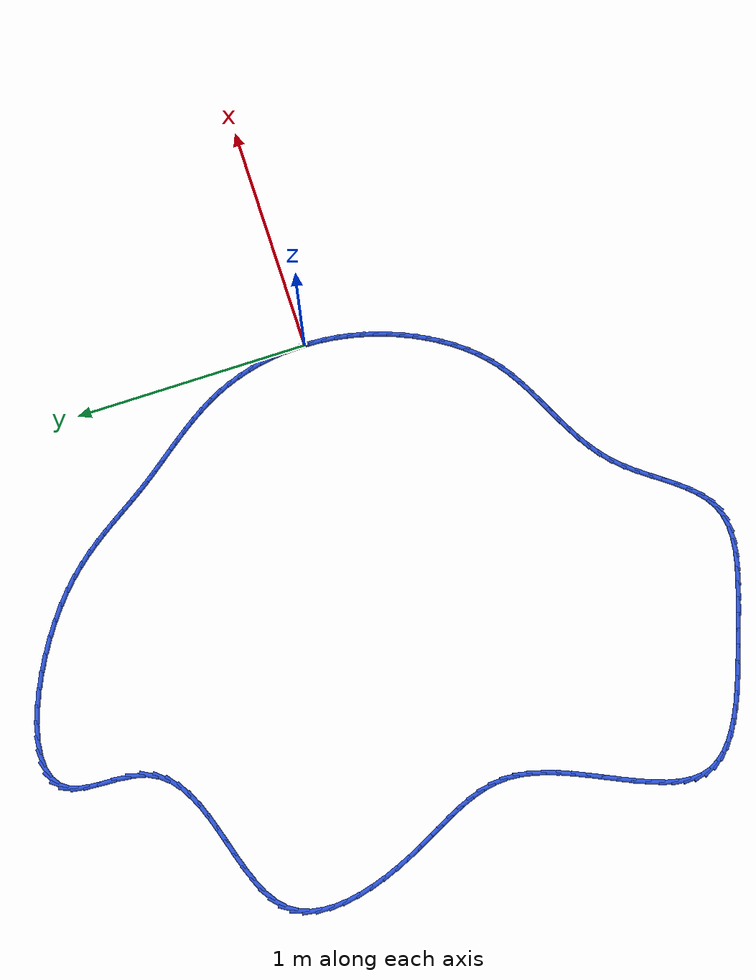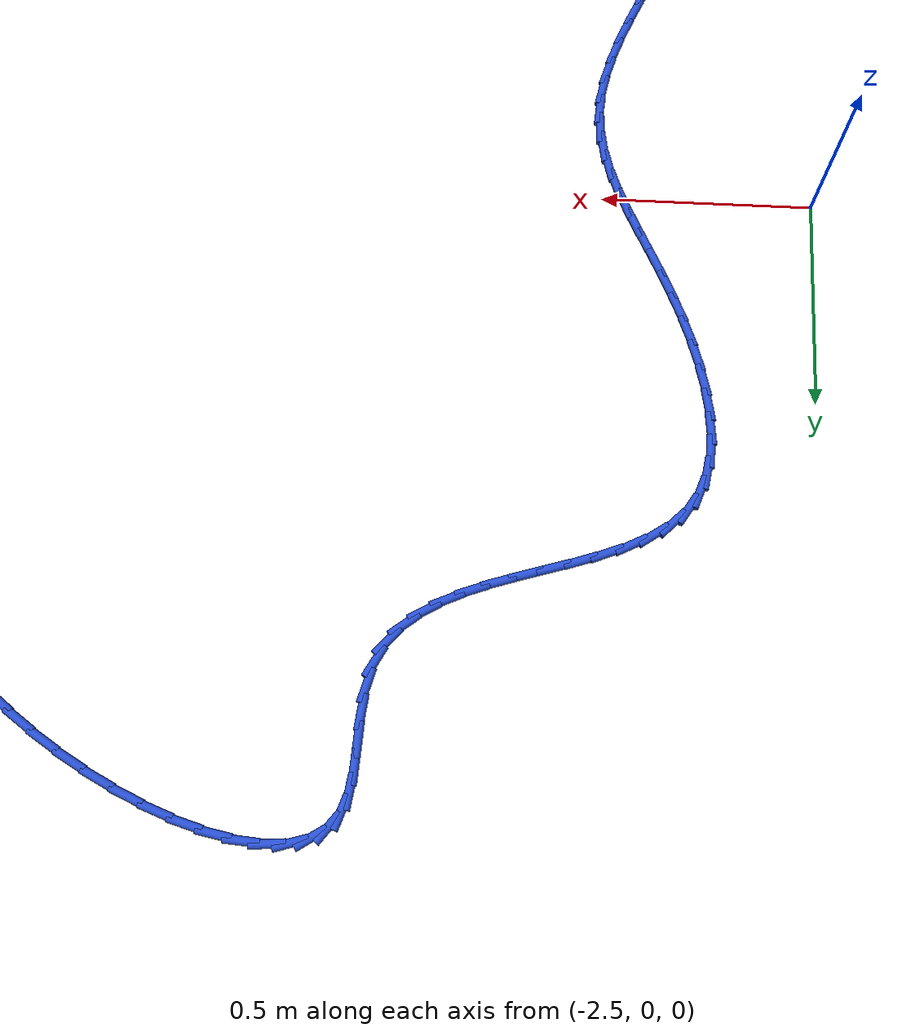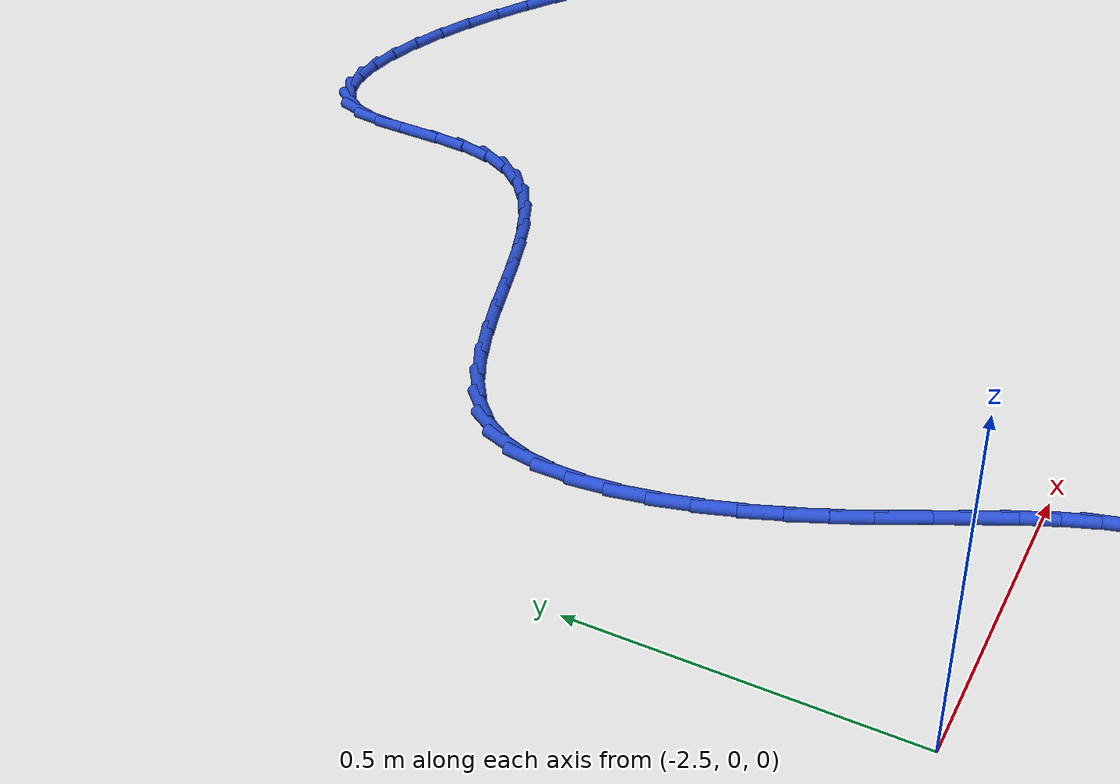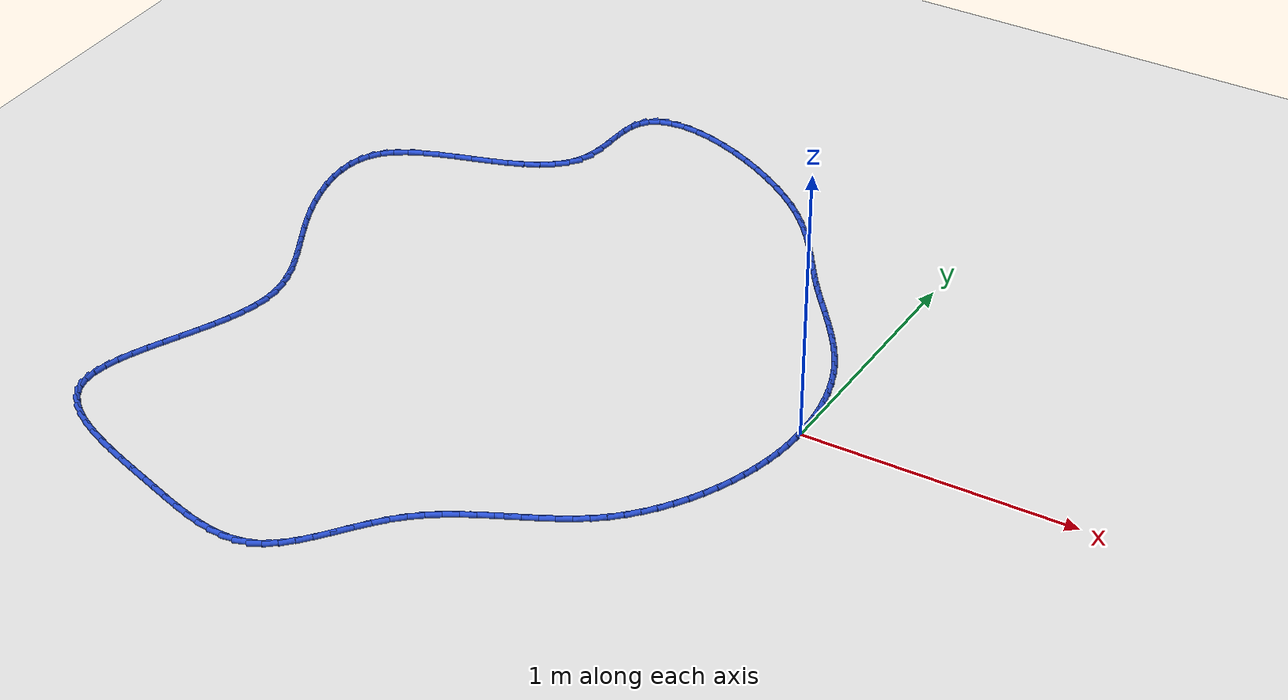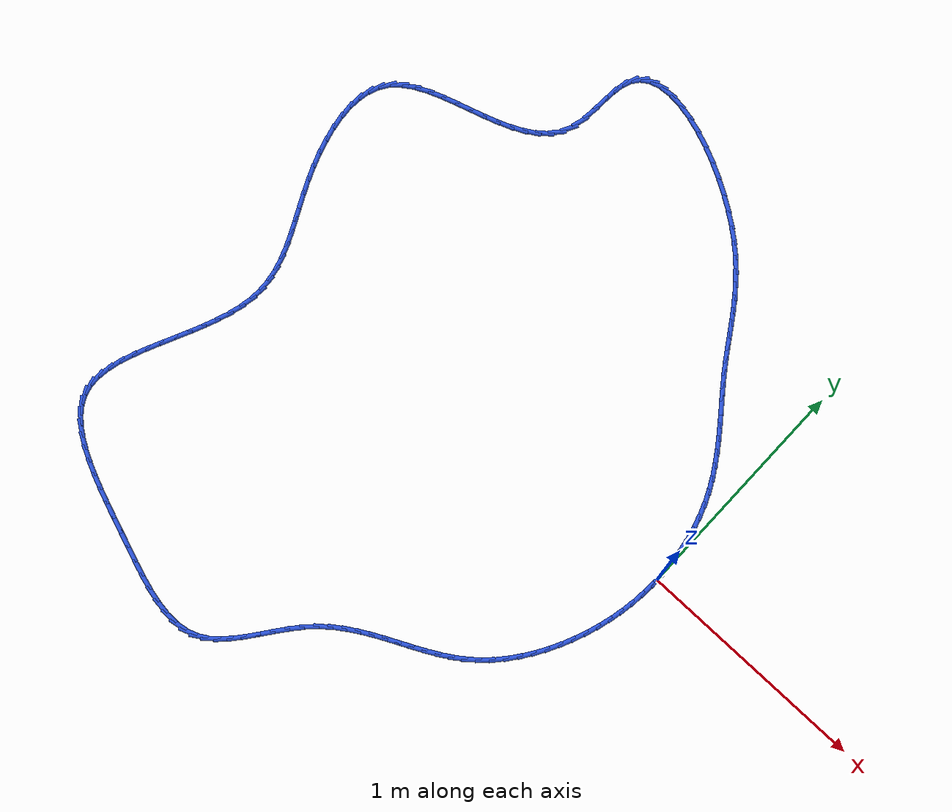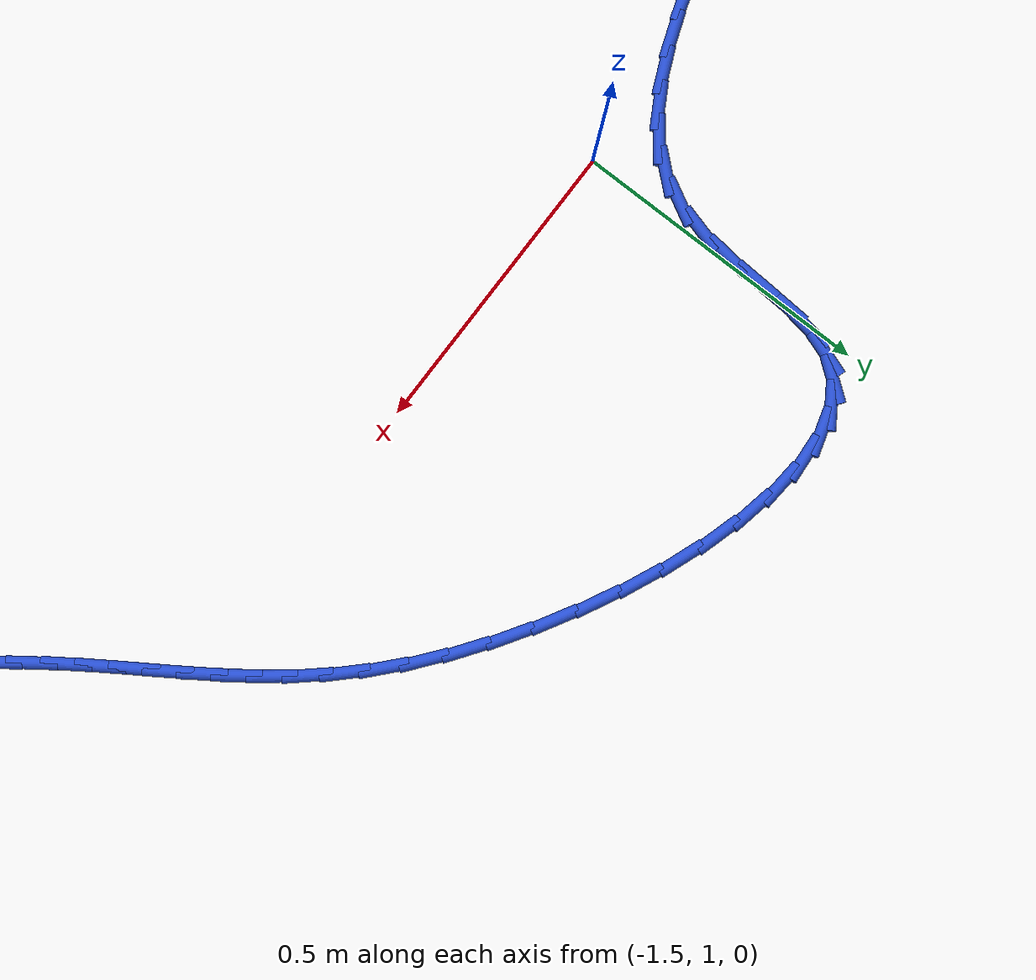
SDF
<sdf version="1.6">
 <world name="default">
  <light name="sun" type="directional">
   <pose>0 0 10 0 -0 0</pose>
   <diffuse>0.8 0.8 0.8 1</diffuse>
   <specular>0.2 0.2 0.2 1</specular>
   <attenuation>
    <range>1000</range>
    <constant>0.9</constant>
    <linear>0.01</linear>
    <quadratic>0.001</quadratic>
   </attenuation>
   <direction>-0.5 0.1 -0.9</direction>
  </light>
  <model name="ground_plane">
   <static>1</static>
   <link name="link">
    <collision name="collision">
     <geometry><plane><normal>0 0 1</normal><size>100 100</size></plane></geometry>
     <surface><friction><ode><mu>100</mu><mu2>50</mu2></ode></friction></surface>
    </collision>
    <visual name="visual">
     <cast_shadows>0</cast_shadows>
     <geometry><plane><normal>0 0 1</normal><size>100 100</size></plane></geometry>
     <material>
      <script><uri>file://media/materials/scripts/gazebo.material</uri><name>Gazebo/WhiteGlow</name></script>
     </material>
    </visual>
   </link>
  </model>
  <gravity>0 0 -9.8</gravity>
  <magnetic_field>6e-06 2.3e-05 -4.2e-05</magnetic_field>
  <atmosphere type="adiabatic"/>
  <physics name="default_physics" default="0" type="ode">
   <max_step_size>0.001</max_step_size>
   <real_time_factor>1</real_time_factor>
   <real_time_update_rate>1000</real_time_update_rate>
  </physics>
  <scene><ambient>0.4 0.4 0.4 1</ambient><background>0.7 0.7 0.7 1</background><shadows>1</shadows></scene>
  <spherical_coordinates>
   <surface_model>EARTH_WGS84</surface_model>
   <latitude_deg>0</latitude_deg>
   <longitude_deg>0</longitude_deg>
   <elevation>0</elevation>
   <heading_deg>0</heading_deg>
  </spherical_coordinates>
  <model name="line">
   <link name="link_0">
    <pose>4.683753385137379e-17 -2.7755575615628914e-17 0.01 0 1.57 -1.5506919938841304</pose>
    <collision name="collision">
     <geometry><cylinder><radius>0.01</radius><length>0.08</length></cylinder></geometry>
    </collision>
    <visual name="visual">
     <material>
      <script><name>Gazebo/Blue</name><uri>file://media/materials/scripts/gazebo.material</uri></script>
     </material>
     <geometry><cylinder><radius>0.01</radius><length>0.08</length></cylinder></geometry>
    </visual>
   </link>
   <link name="link_1">
    <pose>-0.001116520090543789 0.05552880888172366 0.01 0 1.57 -1.495366794349657</pose>
    <collision name="collision">
     <geometry><cylinder><radius>0.01</radius><length>0.08</length></cylinder></geometry>
    </collision>
    <visual name="visual">
     <material>
      <script><name>Gazebo/Blue</name><uri>file://media/materials/scripts/gazebo.material</uri></script>
     </material>
     <geometry><cylinder><radius>0.01</radius><length>0.08</length></cylinder></geometry>
    </visual>
   </link>
   <link name="link_2">
    <pose>-0.005309508748595053 0.11101150036339982 0.01 0 1.57 -1.4390167244081917</pose>
    <collision name="collision">
     <geometry><cylinder><radius>0.01</radius><length>0.08</length></cylinder></geometry>
    </collision>
    <visual name="visual">
     <material>
      <script><name>Gazebo/Blue</name><uri>file://media/materials/scripts/gazebo.material</uri></script>
     </material>
     <geometry><cylinder><radius>0.01</radius><length>0.08</length></cylinder></geometry>
    </visual>
   </link>
   <link name="link_3">
    <pose>-0.012625676608028148 0.16620796546003416 0.01 0 1.57 -1.3812919054459138</pose>
    <collision name="collision">
     <geometry><cylinder><radius>0.01</radius><length>0.08</length></cylinder></geometry>
    </collision>
    <visual name="visual">
     <material>
      <script><name>Gazebo/Blue</name><uri>file://media/materials/scripts/gazebo.material</uri></script>
     </material>
     <geometry><cylinder><radius>0.01</radius><length>0.08</length></cylinder></geometry>
    </visual>
   </link>
   <link name="link_4">
    <pose>-0.023111734302717485 0.22087809518663248 0.01 0 1.57 -1.3218626975104655</pose>
    <collision name="collision">
     <geometry><cylinder><radius>0.01</radius><length>0.08</length></cylinder></geometry>
    </collision>
    <visual name="visual">
     <material>
      <script><name>Gazebo/Blue</name><uri>file://media/materials/scripts/gazebo.material</uri></script>
     </material>
     <geometry><cylinder><radius>0.01</radius><length>0.08</length></cylinder></geometry>
    </visual>
   </link>
   <link name="link_5">
    <pose>-0.03681439246653747 0.27478178055820035 0.01 0 1.57 -1.2604266667311834</pose>
    <collision name="collision">
     <geometry><cylinder><radius>0.01</radius><length>0.08</length></cylinder></geometry>
    </collision>
    <visual name="visual">
     <material>
      <script><name>Gazebo/Blue</name><uri>file://media/materials/scripts/gazebo.material</uri></script>
     </material>
     <geometry><cylinder><radius>0.01</radius><length>0.08</length></cylinder></geometry>
    </visual>
   </link>
   <link name="link_6">
    <pose>-0.05378036173336253 0.32767891258974374 0.01 0 1.57 -1.1967187652436428</pose>
    <collision name="collision">
     <geometry><cylinder><radius>0.01</radius><length>0.08</length></cylinder></geometry>
    </collision>
    <visual name="visual">
     <material>
      <script><name>Gazebo/Blue</name><uri>file://media/materials/scripts/gazebo.material</uri></script>
     </material>
     <geometry><cylinder><radius>0.01</radius><length>0.08</length></cylinder></geometry>
    </visual>
   </link>
   <link name="link_7">
    <pose>-0.0740563527370671 0.3793293822962682 0.01 0 1.57 -1.130738590442869</pose>
    <collision name="collision">
     <geometry><cylinder><radius>0.01</radius><length>0.08</length></cylinder></geometry>
    </collision>
    <visual name="visual">
     <material>
      <script><name>Gazebo/Blue</name><uri>file://media/materials/scripts/gazebo.material</uri></script>
     </material>
     <geometry><cylinder><radius>0.01</radius><length>0.08</length></cylinder></geometry>
    </visual>
   </link>
   <link name="link_8">
    <pose>-0.0976792400495211 0.42949999721846877 0.01 0 1.57 -1.068445978851124</pose>
    <collision name="collision">
     <geometry><cylinder><radius>0.01</radius><length>0.08</length></cylinder></geometry>
    </collision>
    <visual name="visual">
     <material>
      <script><name>Gazebo/Blue</name><uri>file://media/materials/scripts/gazebo.material</uri></script>
     </material>
     <geometry><cylinder><radius>0.01</radius><length>0.08</length></cylinder></geometry>
    </visual>
   </link>
   <link name="link_9">
    <pose>-0.12440739023265601 0.47815340626165503 0.01 0 1.57 -1.0166590960415076</pose>
    <collision name="collision">
     <geometry><cylinder><radius>0.01</radius><length>0.08</length></cylinder></geometry>
    </collision>
    <visual name="visual">
     <material>
      <script><name>Gazebo/Blue</name><uri>file://media/materials/scripts/gazebo.material</uri></script>
     </material>
     <geometry><cylinder><radius>0.01</radius><length>0.08</length></cylinder></geometry>
    </visual>
   </link>
   <link name="link_10">
    <pose>-0.1536880923540233 0.5254710019177713 0.01 0 1.57 -0.9756159868433226</pose>
    <collision name="collision">
     <geometry><cylinder><radius>0.01</radius><length>0.08</length></cylinder></geometry>
    </collision>
    <visual name="visual">
     <material>
      <script><name>Gazebo/Blue</name><uri>file://media/materials/scripts/gazebo.material</uri></script>
     </material>
     <geometry><cylinder><radius>0.01</radius><length>0.08</length></cylinder></geometry>
    </visual>
   </link>
   <link name="link_11">
    <pose>-0.18495226053611355 0.5716456912186374 0.01 0 1.57 -0.9450748598798837</pose>
    <collision name="collision">
     <geometry><cylinder><radius>0.01</radius><length>0.08</length></cylinder></geometry>
    </collision>
    <visual name="visual">
     <material>
      <script><name>Gazebo/Blue</name><uri>file://media/materials/scripts/gazebo.material</uri></script>
     </material>
     <geometry><cylinder><radius>0.01</radius><length>0.08</length></cylinder></geometry>
    </visual>
   </link>
   <link name="link_12">
    <pose>-0.2176308089014174 0.6168703811960738 0.01 0 1.57 -0.9248078906574905</pose>
    <collision name="collision">
     <geometry><cylinder><radius>0.01</radius><length>0.08</length></cylinder></geometry>
    </collision>
    <visual name="visual">
     <material>
      <script><name>Gazebo/Blue</name><uri>file://media/materials/scripts/gazebo.material</uri></script>
     </material>
     <geometry><cylinder><radius>0.01</radius><length>0.08</length></cylinder></geometry>
    </visual>
   </link>
   <link name="link_13">
    <pose>-0.2511546515724252 0.6613379788819003 0.01 0 1.57 -0.9146973530127385</pose>
    <collision name="collision">
     <geometry><cylinder><radius>0.01</radius><length>0.08</length></cylinder></geometry>
    </collision>
    <visual name="visual">
     <material>
      <script><name>Gazebo/Blue</name><uri>file://media/materials/scripts/gazebo.material</uri></script>
     </material>
     <geometry><cylinder><radius>0.01</radius><length>0.08</length></cylinder></geometry>
    </visual>
   </link>
   <link name="link_14">
    <pose>-0.2849547026716277 0.705241391307937 0.01 0 1.57 -0.9147989040670265</pose>
    <collision name="collision">
     <geometry><cylinder><radius>0.01</radius><length>0.08</length></cylinder></geometry>
    </collision>
    <visual name="visual">
     <material>
      <script><name>Gazebo/Blue</name><uri>file://media/materials/scripts/gazebo.material</uri></script>
     </material>
     <geometry><cylinder><radius>0.01</radius><length>0.08</length></cylinder></geometry>
    </visual>
   </link>
   <link name="link_15">
    <pose>-0.31846187632151546 0.7487735255060043 0.01 0 1.57 -0.9253805309040767</pose>
    <collision name="collision">
     <geometry><cylinder><radius>0.01</radius><length>0.08</length></cylinder></geometry>
    </collision>
    <visual name="visual">
     <material>
      <script><name>Gazebo/Blue</name><uri>file://media/materials/scripts/gazebo.material</uri></script>
     </material>
     <geometry><cylinder><radius>0.01</radius><length>0.08</length></cylinder></geometry>
    </visual>
   </link>
   <link name="link_16">
    <pose>-0.3511070866445789 0.7921272885079219 0.01 0 1.57 -0.9468921747444471</pose>
    <collision name="collision">
     <geometry><cylinder><radius>0.01</radius><length>0.08</length></cylinder></geometry>
    </collision>
    <visual name="visual">
     <material>
      <script><name>Gazebo/Blue</name><uri>file://media/materials/scripts/gazebo.material</uri></script>
     </material>
     <geometry><cylinder><radius>0.01</radius><length>0.08</length></cylinder></geometry>
    </visual>
   </link>
   <link name="link_17">
    <pose>-0.3823240401182465 0.8354950418155851 0.01 0 1.57 -0.9729804366898012</pose>
    <collision name="collision">
     <geometry><cylinder><radius>0.01</radius><length>0.08</length></cylinder></geometry>
    </collision>
    <visual name="visual">
     <material>
      <script><name>Gazebo/Blue</name><uri>file://media/materials/scripts/gazebo.material</uri></script>
     </material>
     <geometry><cylinder><radius>0.01</radius><length>0.08</length></cylinder></geometry>
    </visual>
   </link>
   <link name="link_18">
    <pose>-0.41194249559819796 0.8789917719449142 0.01 0 1.57 -0.9892312899376181</pose>
    <collision name="collision">
     <geometry><cylinder><radius>0.01</radius><length>0.08</length></cylinder></geometry>
    </collision>
    <visual name="visual">
     <material>
      <script><name>Gazebo/Blue</name><uri>file://media/materials/scripts/gazebo.material</uri></script>
     </material>
     <geometry><cylinder><radius>0.01</radius><length>0.08</length></cylinder></geometry>
    </visual>
   </link>
   <link name="link_19">
    <pose>-0.44059486940551335 0.9225756538042263 0.01 0 1.57 -0.9933077386441407</pose>
    <collision name="collision">
     <geometry><cylinder><radius>0.01</radius><length>0.08</length></cylinder></geometry>
    </collision>
    <visual name="visual">
     <material>
      <script><name>Gazebo/Blue</name><uri>file://media/materials/scripts/gazebo.material</uri></script>
     </material>
     <geometry><cylinder><radius>0.01</radius><length>0.08</length></cylinder></geometry>
    </visual>
   </link>
   <link name="link_20">
    <pose>-0.46901064681831384 0.9661858983728185 0.01 0 1.57 -0.9850512075724858</pose>
    <collision name="collision">
     <geometry><cylinder><radius>0.01</radius><length>0.08</length></cylinder></geometry>
    </collision>
    <visual name="visual">
     <material>
      <script><name>Gazebo/Blue</name><uri>file://media/materials/scripts/gazebo.material</uri></script>
     </material>
     <geometry><cylinder><radius>0.01</radius><length>0.08</length></cylinder></geometry>
    </visual>
   </link>
   <link name="link_21">
    <pose>-0.4979193131147216 1.0097617166299877 0.01 0 1.57 -0.9647996219319948</pose>
    <collision name="collision">
     <geometry><cylinder><radius>0.01</radius><length>0.08</length></cylinder></geometry>
    </collision>
    <visual name="visual">
     <material>
      <script><name>Gazebo/Blue</name><uri>file://media/materials/scripts/gazebo.material</uri></script>
     </material>
     <geometry><cylinder><radius>0.01</radius><length>0.08</length></cylinder></geometry>
    </visual>
   </link>
   <link name="link_22">
    <pose>-0.5280503535728575 1.0532423195550304 0.01 0 1.57 -0.933387570112398</pose>
    <collision name="collision">
     <geometry><cylinder><radius>0.01</radius><length>0.08</length></cylinder></geometry>
    </collision>
    <visual name="visual">
     <material>
      <script><name>Gazebo/Blue</name><uri>file://media/materials/scripts/gazebo.material</uri></script>
     </material>
     <geometry><cylinder><radius>0.01</radius><length>0.08</length></cylinder></geometry>
    </visual>
   </link>
   <link name="link_23">
    <pose>-0.5601332534708434 1.0965669181272437 0.01 0 1.57 -0.8921354442786551</pose>
    <collision name="collision">
     <geometry><cylinder><radius>0.01</radius><length>0.08</length></cylinder></geometry>
    </collision>
    <visual name="visual">
     <material>
      <script><name>Gazebo/Blue</name><uri>file://media/materials/scripts/gazebo.material</uri></script>
     </material>
     <geometry><cylinder><radius>0.01</radius><length>0.08</length></cylinder></geometry>
    </visual>
   </link>
   <link name="link_24">
    <pose>-0.5948974980868004 1.1396747233259235 0.01 0 1.57 -0.8428022339938956</pose>
    <collision name="collision">
     <geometry><cylinder><radius>0.01</radius><length>0.08</length></cylinder></geometry>
    </collision>
    <visual name="visual">
     <material>
      <script><name>Gazebo/Blue</name><uri>file://media/materials/scripts/gazebo.material</uri></script>
     </material>
     <geometry><cylinder><radius>0.01</radius><length>0.08</length></cylinder></geometry>
    </visual>
   </link>
   <link name="link_25">
    <pose>-0.6330725726988508 1.1825049461303678 0.01 0 1.57 -0.7874788966688654</pose>
    <collision name="collision">
     <geometry><cylinder><radius>0.01</radius><length>0.08</length></cylinder></geometry>
    </collision>
    <visual name="visual">
     <material>
      <script><name>Gazebo/Blue</name><uri>file://media/materials/scripts/gazebo.material</uri></script>
     </material>
     <geometry><cylinder><radius>0.01</radius><length>0.08</length></cylinder></geometry>
    </visual>
   </link>
   <link name="link_26">
    <pose>-0.6753879625851154 1.2249967975198726 0.01 0 1.57 -0.7284189088602177</pose>
    <collision name="collision">
     <geometry><cylinder><radius>0.01</radius><length>0.08</length></cylinder></geometry>
    </collision>
    <visual name="visual">
     <material>
      <script><name>Gazebo/Blue</name><uri>file://media/materials/scripts/gazebo.material</uri></script>
     </material>
     <geometry><cylinder><radius>0.01</radius><length>0.08</length></cylinder></geometry>
    </visual>
   </link>
   <link name="link_27">
    <pose>-0.7225731530237162 1.2670894884737347 0.01 0 1.57 -0.6684847782224723</pose>
    <collision name="collision">
     <geometry><cylinder><radius>0.01</radius><length>0.08</length></cylinder></geometry>
    </collision>
    <visual name="visual">
     <material>
      <script><name>Gazebo/Blue</name><uri>file://media/materials/scripts/gazebo.material</uri></script>
     </material>
     <geometry><cylinder><radius>0.01</radius><length>0.08</length></cylinder></geometry>
    </visual>
   </link>
   <link name="link_28">
    <pose>-0.7752221834271208 1.3086712111539796 0.01 0 1.57 -0.6135340071690958</pose>
    <collision name="collision">
     <geometry><cylinder><radius>0.01</radius><length>0.08</length></cylinder></geometry>
    </collision>
    <visual name="visual">
     <material>
      <script><name>Gazebo/Blue</name><uri>file://media/materials/scripts/gazebo.material</uri></script>
     </material>
     <geometry><cylinder><radius>0.01</radius><length>0.08</length></cylinder></geometry>
    </visual>
   </link>
   <link name="link_29">
    <pose>-0.8327627385294791 1.3491908232629193 0.01 0 1.57 -0.5631852698814351</pose>
    <collision name="collision">
     <geometry><cylinder><radius>0.01</radius><length>0.08</length></cylinder></geometry>
    </collision>
    <visual name="visual">
     <material>
      <script><name>Gazebo/Blue</name><uri>file://media/materials/scripts/gazebo.material</uri></script>
     </material>
     <geometry><cylinder><radius>0.01</radius><length>0.08</length></cylinder></geometry>
    </visual>
   </link>
   <link name="link_30">
    <pose>-0.8940272229676131 1.3878729564892882 0.01 0 1.57 -0.514422191157868</pose>
    <collision name="collision">
     <geometry><cylinder><radius>0.01</radius><length>0.08</length></cylinder></geometry>
    </collision>
    <visual name="visual">
     <material>
      <script><name>Gazebo/Blue</name><uri>file://media/materials/scripts/gazebo.material</uri></script>
     </material>
     <geometry><cylinder><radius>0.01</radius><length>0.08</length></cylinder></geometry>
    </visual>
   </link>
   <link name="link_31">
    <pose>-0.9578432767817597 1.4239404478263444 0.01 0 1.57 -0.4646049477476544</pose>
    <collision name="collision">
     <geometry><cylinder><radius>0.01</radius><length>0.08</length></cylinder></geometry>
    </collision>
    <visual name="visual">
     <material>
      <script><name>Gazebo/Blue</name><uri>file://media/materials/scripts/gazebo.material</uri></script>
     </material>
     <geometry><cylinder><radius>0.01</radius><length>0.08</length></cylinder></geometry>
    </visual>
   </link>
   <link name="link_32">
    <pose>-1.0230385400121553 1.4566161342673443 0.01 0 1.57 -0.41104020291991156</pose>
    <collision name="collision">
     <geometry><cylinder><radius>0.01</radius><length>0.08</length></cylinder></geometry>
    </collision>
    <visual name="visual">
     <material>
      <script><name>Gazebo/Blue</name><uri>file://media/materials/scripts/gazebo.material</uri></script>
     </material>
     <geometry><cylinder><radius>0.01</radius><length>0.08</length></cylinder></geometry>
    </visual>
   </link>
   <link name="link_33">
    <pose>-1.0884406526990362 1.4851228528055453 0.01 0 1.57 -0.35053934003539816</pose>
    <collision name="collision">
     <geometry><cylinder><radius>0.01</radius><length>0.08</length></cylinder></geometry>
    </collision>
    <visual name="visual">
     <material>
      <script><name>Gazebo/Blue</name><uri>file://media/materials/scripts/gazebo.material</uri></script>
     </material>
     <geometry><cylinder><radius>0.01</radius><length>0.08</length></cylinder></geometry>
    </visual>
   </link>
   <link name="link_34">
    <pose>-1.1528772548826391 1.508683440434204 0.01 0 1.57 -0.2788583950742498</pose>
    <collision name="collision">
     <geometry><cylinder><radius>0.01</radius><length>0.08</length></cylinder></geometry>
    </collision>
    <visual name="visual">
     <material>
      <script><name>Gazebo/Blue</name><uri>file://media/materials/scripts/gazebo.material</uri></script>
     </material>
     <geometry><cylinder><radius>0.01</radius><length>0.08</length></cylinder></geometry>
    </visual>
   </link>
   <link name="link_35">
    <pose>-1.2151759866031997 1.5265207341465774 0.01 0 1.57 -0.18987212111653612</pose>
    <collision name="collision">
     <geometry><cylinder><radius>0.01</radius><length>0.08</length></cylinder></geometry>
    </collision>
    <visual name="visual">
     <material>
      <script><name>Gazebo/Blue</name><uri>file://media/materials/scripts/gazebo.material</uri></script>
     </material>
     <geometry><cylinder><radius>0.01</radius><length>0.08</length></cylinder></geometry>
    </visual>
   </link>
   <link name="link_36">
    <pose>-1.2741644879009553 1.5378575709359226 0.01 0 1.57 -0.07433574130946816</pose>
    <collision name="collision">
     <geometry><cylinder><radius>0.01</radius><length>0.08</length></cylinder></geometry>
    </collision>
    <visual name="visual">
     <material>
      <script><name>Gazebo/Blue</name><uri>file://media/materials/scripts/gazebo.material</uri></script>
     </material>
     <geometry><cylinder><radius>0.01</radius><length>0.08</length></cylinder></geometry>
    </visual>
   </link>
   <link name="link_37">
    <pose>-1.3286703988161412 1.5419167877954965 0.01 0 1.57 0.08160928326728085</pose>
    <collision name="collision">
     <geometry><cylinder><radius>0.01</radius><length>0.08</length></cylinder></geometry>
    </collision>
    <visual name="visual">
     <material>
      <script><name>Gazebo/Blue</name><uri>file://media/materials/scripts/gazebo.material</uri></script>
     </material>
     <geometry><cylinder><radius>0.01</radius><length>0.08</length></cylinder></geometry>
    </visual>
   </link>
   <link name="link_38">
    <pose>-1.3775213593889948 1.5379212217185558 0.01 0 1.57 0.29626181070779095</pose>
    <collision name="collision">
     <geometry><cylinder><radius>0.01</radius><length>0.08</length></cylinder></geometry>
    </collision>
    <visual name="visual">
     <material>
      <script><name>Gazebo/Blue</name><uri>file://media/materials/scripts/gazebo.material</uri></script>
     </material>
     <geometry><cylinder><radius>0.01</radius><length>0.08</length></cylinder></geometry>
    </visual>
   </link>
   <link name="link_39">
    <pose>-1.4195450096597522 1.5250937096983583 0.01 0 1.57 0.5829797039190706</pose>
    <collision name="collision">
     <geometry><cylinder><radius>0.01</radius><length>0.08</length></cylinder></geometry>
    </collision>
    <visual name="visual">
     <material>
      <script><name>Gazebo/Blue</name><uri>file://media/materials/scripts/gazebo.material</uri></script>
     </material>
     <geometry><cylinder><radius>0.01</radius><length>0.08</length></cylinder></geometry>
    </visual>
   </link>
   <link name="link_40">
    <pose>-1.4535689896686494 1.5026570887281605 0.01 0 1.57 0.9227330337978142</pose>
    <collision name="collision">
     <geometry><cylinder><radius>0.01</radius><length>0.08</length></cylinder></geometry>
    </collision>
    <visual name="visual">
     <material>
      <script><name>Gazebo/Blue</name><uri>file://media/materials/scripts/gazebo.material</uri></script>
     </material>
     <geometry><cylinder><radius>0.01</radius><length>0.08</length></cylinder></geometry>
    </visual>
   </link>
   <link name="link_41">
    <pose>-1.4784209394559236 1.4698341958012195 0.01 0 1.57 1.2414089775007526</pose>
    <collision name="collision">
     <geometry><cylinder><radius>0.01</radius><length>0.08</length></cylinder></geometry>
    </collision>
    <visual name="visual">
     <material>
      <script><name>Gazebo/Blue</name><uri>file://media/materials/scripts/gazebo.material</uri></script>
     </material>
     <geometry><cylinder><radius>0.01</radius><length>0.08</length></cylinder></geometry>
    </visual>
   </link>
   <link name="link_42">
    <pose>-1.4933390667105304 1.4261935855369068 0.01 0 1.57 1.431590275779909</pose>
    <collision name="collision">
     <geometry><cylinder><radius>0.01</radius><length>0.08</length></cylinder></geometry>
    </collision>
    <visual name="visual">
     <material>
      <script><name>Gazebo/Blue</name><uri>file://media/materials/scripts/gazebo.material</uri></script>
     </material>
     <geometry><cylinder><radius>0.01</radius><length>0.08</length></cylinder></geometry>
    </visual>
   </link>
   <link name="link_43">
    <pose>-1.5006637941841112 1.373916026231228 0.01 0 1.57 1.5102315090465772</pose>
    <collision name="collision">
     <geometry><cylinder><radius>0.01</radius><length>0.08</length></cylinder></geometry>
    </collision>
    <visual name="visual">
     <material>
      <script><name>Gazebo/Blue</name><uri>file://media/materials/scripts/gazebo.material</uri></script>
     </material>
     <geometry><cylinder><radius>0.01</radius><length>0.08</length></cylinder></geometry>
    </visual>
   </link>
   <link name="link_44">
    <pose>-1.504152973015457 1.3163758287759606 0.01 0 1.57 1.5133263690842145</pose>
    <collision name="collision">
     <geometry><cylinder><radius>0.01</radius><length>0.08</length></cylinder></geometry>
    </collision>
    <visual name="visual">
     <material>
      <script><name>Gazebo/Blue</name><uri>file://media/materials/scripts/gazebo.material</uri></script>
     </material>
     <geometry><cylinder><radius>0.01</radius><length>0.08</length></cylinder></geometry>
    </visual>
   </link>
   <link name="link_45">
    <pose>-1.5075717399099797 1.2569534388589496 0.01 0 1.57 1.4486011358255213</pose>
    <collision name="collision">
     <geometry><cylinder><radius>0.01</radius><length>0.08</length></cylinder></geometry>
    </collision>
    <visual name="visual">
     <material>
      <script><name>Gazebo/Blue</name><uri>file://media/materials/scripts/gazebo.material</uri></script>
     </material>
     <geometry><cylinder><radius>0.01</radius><length>0.08</length></cylinder></geometry>
    </visual>
   </link>
   <link name="link_46">
    <pose>-1.514685231573094 1.1990293021680443 0.01 0 1.57 1.3026847288186552</pose>
    <collision name="collision">
     <geometry><cylinder><radius>0.01</radius><length>0.08</length></cylinder></geometry>
    </collision>
    <visual name="visual">
     <material>
      <script><name>Gazebo/Blue</name><uri>file://media/materials/scripts/gazebo.material</uri></script>
     </material>
     <geometry><cylinder><radius>0.01</radius><length>0.08</length></cylinder></geometry>
    </visual>
   </link>
   <link name="link_47">
    <pose>-1.529258272828922 1.1459836012198021 0.01 0 1.57 1.0746102355254372</pose>
    <collision name="collision">
     <geometry><cylinder><radius>0.01</radius><length>0.08</length></cylinder></geometry>
    </collision>
    <visual name="visual">
     <material>
      <script><name>Gazebo/Blue</name><uri>file://media/materials/scripts/gazebo.material</uri></script>
     </material>
     <geometry><cylinder><radius>0.01</radius><length>0.08</length></cylinder></geometry>
    </visual>
   </link>
   <link name="link_48">
    <pose>-1.5539907224668497 1.1002978801974856 0.01 0 1.57 0.8484842545476882</pose>
    <collision name="collision">
     <geometry><cylinder><radius>0.01</radius><length>0.08</length></cylinder></geometry>
    </collision>
    <visual name="visual">
     <material>
      <script><name>Gazebo/Blue</name><uri>file://media/materials/scripts/gazebo.material</uri></script>
     </material>
     <geometry><cylinder><radius>0.01</radius><length>0.08</length></cylinder></geometry>
    </visual>
   </link>
   <link name="link_49">
    <pose>-1.5881371606472665 1.0615464924971214 0.01 0 1.57 0.6620757254218073</pose>
    <collision name="collision">
     <geometry><cylinder><radius>0.01</radius><length>0.08</length></cylinder></geometry>
    </collision>
    <visual name="visual">
     <material>
      <script><name>Gazebo/Blue</name><uri>file://media/materials/scripts/gazebo.material</uri></script>
     </material>
     <geometry><cylinder><radius>0.01</radius><length>0.08</length></cylinder></geometry>
    </visual>
   </link>
   <link name="link_50">
    <pose>-1.6302567318096302 1.0287169697976213 0.01 0 1.57 0.520989119092816</pose>
    <collision name="collision">
     <geometry><cylinder><radius>0.01</radius><length>0.08</length></cylinder></geometry>
    </collision>
    <visual name="visual">
     <material>
      <script><name>Gazebo/Blue</name><uri>file://media/materials/scripts/gazebo.material</uri></script>
     </material>
     <geometry><cylinder><radius>0.01</radius><length>0.08</length></cylinder></geometry>
    </visual>
   </link>
   <link name="link_51">
    <pose>-1.6789085803933976 1.0007968437778978 0.01 0 1.57 0.4203556389696027</pose>
    <collision name="collision">
     <geometry><cylinder><radius>0.01</radius><length>0.08</length></cylinder></geometry>
    </collision>
    <visual name="visual">
     <material>
      <script><name>Gazebo/Blue</name><uri>file://media/materials/scripts/gazebo.material</uri></script>
     </material>
     <geometry><cylinder><radius>0.01</radius><length>0.08</length></cylinder></geometry>
    </visual>
   </link>
   <link name="link_52">
    <pose>-1.7326518508380266 0.9767736461168623 0.01 0 1.57 0.35289281265418443</pose>
    <collision name="collision">
     <geometry><cylinder><radius>0.01</radius><length>0.08</length></cylinder></geometry>
    </collision>
    <visual name="visual">
     <material>
      <script><name>Gazebo/Blue</name><uri>file://media/materials/scripts/gazebo.material</uri></script>
     </material>
     <geometry><cylinder><radius>0.01</radius><length>0.08</length></cylinder></geometry>
    </visual>
   </link>
   <link name="link_53">
    <pose>-1.7900456875829733 0.9556349084934267 0.01 0 1.57 0.31264673916821545</pose>
    <collision name="collision">
     <geometry><cylinder><radius>0.01</radius><length>0.08</length></cylinder></geometry>
    </collision>
    <visual name="visual">
     <material>
      <script><name>Gazebo/Blue</name><uri>file://media/materials/scripts/gazebo.material</uri></script>
     </material>
     <geometry><cylinder><radius>0.01</radius><length>0.08</length></cylinder></geometry>
    </visual>
   </link>
   <link name="link_54">
    <pose>-1.8496492350676965 0.936368162586503 0.01 0 1.57 0.29594122671655926</pose>
    <collision name="collision">
     <geometry><cylinder><radius>0.01</radius><length>0.08</length></cylinder></geometry>
    </collision>
    <visual name="visual">
     <material>
      <script><name>Gazebo/Blue</name><uri>file://media/materials/scripts/gazebo.material</uri></script>
     </material>
     <geometry><cylinder><radius>0.01</radius><length>0.08</length></cylinder></geometry>
    </visual>
   </link>
   <link name="link_55">
    <pose>-1.910021637731653 0.9179609400750037 0.01 0 1.57 0.3014160509819723</pose>
    <collision name="collision">
     <geometry><cylinder><radius>0.01</radius><length>0.08</length></cylinder></geometry>
    </collision>
    <visual name="visual">
     <material>
      <script><name>Gazebo/Blue</name><uri>file://media/materials/scripts/gazebo.material</uri></script>
     </material>
     <geometry><cylinder><radius>0.01</radius><length>0.08</length></cylinder></geometry>
    </visual>
   </link>
   <link name="link_56">
    <pose>-1.9697220400142996 0.8994007726378398 0.01 0 1.57 0.33000643419502806</pose>
    <collision name="collision">
     <geometry><cylinder><radius>0.01</radius><length>0.08</length></cylinder></geometry>
    </collision>
    <visual name="visual">
     <material>
      <script><name>Gazebo/Blue</name><uri>file://media/materials/scripts/gazebo.material</uri></script>
     </material>
     <geometry><cylinder><radius>0.01</radius><length>0.08</length></cylinder></geometry>
    </visual>
   </link>
   <link name="link_57">
    <pose>-2.027309586355094 0.8796751919539239 0.01 0 1.57 0.3851233886856084</pose>
    <collision name="collision">
     <geometry><cylinder><radius>0.01</radius><length>0.08</length></cylinder></geometry>
    </collision>
    <visual name="visual">
     <material>
      <script><name>Gazebo/Blue</name><uri>file://media/materials/scripts/gazebo.material</uri></script>
     </material>
     <geometry><cylinder><radius>0.01</radius><length>0.08</length></cylinder></geometry>
    </visual>
   </link>
   <link name="link_58">
    <pose>-2.081343421193494 0.857771729702167 0.01 0 1.57 0.4729705070123115</pose>
    <collision name="collision">
     <geometry><cylinder><radius>0.01</radius><length>0.08</length></cylinder></geometry>
    </collision>
    <visual name="visual">
     <material>
      <script><name>Gazebo/Blue</name><uri>file://media/materials/scripts/gazebo.material</uri></script>
     </material>
     <geometry><cylinder><radius>0.01</radius><length>0.08</length></cylinder></geometry>
    </visual>
   </link>
   <link name="link_59">
    <pose>-2.130382688968956 0.832677917561482 0.01 0 1.57 0.6023907293510983</pose>
    <collision name="collision">
     <geometry><cylinder><radius>0.01</radius><length>0.08</length></cylinder></geometry>
    </collision>
    <visual name="visual">
     <material>
      <script><name>Gazebo/Blue</name><uri>file://media/materials/scripts/gazebo.material</uri></script>
     </material>
     <geometry><cylinder><radius>0.01</radius><length>0.08</length></cylinder></geometry>
    </visual>
   </link>
   <link name="link_60">
    <pose>-2.1729865341209385 0.8033812872107806 0.01 0 1.57 0.7822836198326191</pose>
    <collision name="collision">
     <geometry><cylinder><radius>0.01</radius><length>0.08</length></cylinder></geometry>
    </collision>
    <visual name="visual">
     <material>
      <script><name>Gazebo/Blue</name><uri>file://media/materials/scripts/gazebo.material</uri></script>
     </material>
     <geometry><cylinder><radius>0.01</radius><length>0.08</length></cylinder></geometry>
    </visual>
   </link>
   <link name="link_61">
    <pose>-2.2077141010888974 0.7688693703289745 0.01 0 1.57 1.0095461562873214</pose>
    <collision name="collision">
     <geometry><cylinder><radius>0.01</radius><length>0.08</length></cylinder></geometry>
    </collision>
    <visual name="visual">
     <material>
      <script><name>Gazebo/Blue</name><uri>file://media/materials/scripts/gazebo.material</uri></script>
     </material>
     <geometry><cylinder><radius>0.01</radius><length>0.08</length></cylinder></geometry>
    </visual>
   </link>
   <link name="link_62">
    <pose>-2.233254900040821 0.7282441042411204 0.01 0 1.57 1.2311875582966627</pose>
    <collision name="collision">
     <geometry><cylinder><radius>0.01</radius><length>0.08</length></cylinder></geometry>
    </collision>
    <visual name="visual">
     <material>
      <script><name>Gazebo/Blue</name><uri>file://media/materials/scripts/gazebo.material</uri></script>
     </material>
     <geometry><cylinder><radius>0.01</radius><length>0.08</length></cylinder></geometry>
    </visual>
   </link>
   <link name="link_63">
    <pose>-2.249662015348921 0.681804064297169 0.01 0 1.57 1.4132793351795019</pose>
    <collision name="collision">
     <geometry><cylinder><radius>0.01</radius><length>0.08</length></cylinder></geometry>
    </collision>
    <visual name="visual">
     <material>
      <script><name>Gazebo/Blue</name><uri>file://media/materials/scripts/gazebo.material</uri></script>
     </material>
     <geometry><cylinder><radius>0.01</radius><length>0.08</length></cylinder></geometry>
    </visual>
   </link>
   <link name="link_64">
    <pose>-2.257801107251215 0.6305609217505547 0.01 0 1.57 1.557211519991841</pose>
    <collision name="collision">
     <geometry><cylinder><radius>0.01</radius><length>0.08</length></cylinder></geometry>
    </collision>
    <visual name="visual">
     <material>
      <script><name>Gazebo/Blue</name><uri>file://media/materials/scripts/gazebo.material</uri></script>
     </material>
     <geometry><cylinder><radius>0.01</radius><length>0.08</length></cylinder></geometry>
    </visual>
   </link>
   <link name="link_65">
    <pose>-2.2585486582718968 0.5755358452176833 0.01 0 1.57 -1.4713174680209233</pose>
    <collision name="collision">
     <geometry><cylinder><radius>0.01</radius><length>0.08</length></cylinder></geometry>
    </collision>
    <visual name="visual">
     <material>
      <script><name>Gazebo/Blue</name><uri>file://media/materials/scripts/gazebo.material</uri></script>
     </material>
     <geometry><cylinder><radius>0.01</radius><length>0.08</length></cylinder></geometry>
    </visual>
   </link>
   <link name="link_66">
    <pose>-2.2527811509351587 0.5177500033149607 0.01 0 1.57 -1.3814742295364217</pose>
    <collision name="collision">
     <geometry><cylinder><radius>0.01</radius><length>0.08</length></cylinder></geometry>
    </collision>
    <visual name="visual">
     <material>
      <script><name>Gazebo/Blue</name><uri>file://media/materials/scripts/gazebo.material</uri></script>
     </material>
     <geometry><cylinder><radius>0.01</radius><length>0.08</length></cylinder></geometry>
    </visual>
   </link>
   <link name="link_67">
    <pose>-2.241375067765196 0.4582245646587926 0.01 0 1.57 -1.308596155814695</pose>
    <collision name="collision">
     <geometry><cylinder><radius>0.01</radius><length>0.08</length></cylinder></geometry>
    </collision>
    <visual name="visual">
     <material>
      <script><name>Gazebo/Blue</name><uri>file://media/materials/scripts/gazebo.material</uri></script>
     </material>
     <geometry><cylinder><radius>0.01</radius><length>0.08</length></cylinder></geometry>
    </visual>
   </link>
   <link name="link_68">
    <pose>-2.2252068912862017 0.39798069786558604 0.01 0 1.57 -1.2479439187312864</pose>
    <collision name="collision">
     <geometry><cylinder><radius>0.01</radius><length>0.08</length></cylinder></geometry>
    </collision>
    <visual name="visual">
     <material>
      <script><name>Gazebo/Blue</name><uri>file://media/materials/scripts/gazebo.material</uri></script>
     </material>
     <geometry><cylinder><radius>0.01</radius><length>0.08</length></cylinder></geometry>
    </visual>
   </link>
   <link name="link_69">
    <pose>-2.2051531040223704 0.3380395715517465 0.01 0 1.57 -1.1959496456355967</pose>
    <collision name="collision">
     <geometry><cylinder><radius>0.01</radius><length>0.08</length></cylinder></geometry>
    </collision>
    <visual name="visual">
     <material>
      <script><name>Gazebo/Blue</name><uri>file://media/materials/scripts/gazebo.material</uri></script>
     </material>
     <geometry><cylinder><radius>0.01</radius><length>0.08</length></cylinder></geometry>
    </visual>
   </link>
   <link name="link_70">
    <pose>-2.182090188497896 0.2794223543336802 0.01 0 1.57 -1.1510514619495922</pose>
    <collision name="collision">
     <geometry><cylinder><radius>0.01</radius><length>0.08</length></cylinder></geometry>
    </collision>
    <visual name="visual">
     <material>
      <script><name>Gazebo/Blue</name><uri>file://media/materials/scripts/gazebo.material</uri></script>
     </material>
     <geometry><cylinder><radius>0.01</radius><length>0.08</length></cylinder></geometry>
    </visual>
   </link>
   <link name="link_71">
    <pose>-2.1569021951676572 0.22298076695530047 0.01 0 1.57 -1.1187966108798046</pose>
    <collision name="collision">
     <geometry><cylinder><radius>0.01</radius><length>0.08</length></cylinder></geometry>
    </collision>
    <visual name="visual">
     <material>
      <script><name>Gazebo/Blue</name><uri>file://media/materials/scripts/gazebo.material</uri></script>
     </material>
     <geometry><cylinder><radius>0.01</radius><length>0.08</length></cylinder></geometry>
    </visual>
   </link>
   <link name="link_72">
    <pose>-2.1305148843784867 0.1686326351836896 0.01 0 1.57 -1.1023268495115446</pose>
    <collision name="collision">
     <geometry><cylinder><radius>0.01</radius><length>0.08</length></cylinder></geometry>
    </collision>
    <visual name="visual">
     <material>
      <script><name>Gazebo/Blue</name><uri>file://media/materials/scripts/gazebo.material</uri></script>
     </material>
     <geometry><cylinder><radius>0.01</radius><length>0.08</length></cylinder></geometry>
    </visual>
   </link>
   <link name="link_73">
    <pose>-2.1038683084735488 0.11597578339146013 0.01 0 1.57 -1.1027702477081829</pose>
    <collision name="collision">
     <geometry><cylinder><radius>0.01</radius><length>0.08</length></cylinder></geometry>
    </collision>
    <visual name="visual">
     <material>
      <script><name>Gazebo/Blue</name><uri>file://media/materials/scripts/gazebo.material</uri></script>
     </material>
     <geometry><cylinder><radius>0.01</radius><length>0.08</length></cylinder></geometry>
    </visual>
   </link>
   <link name="link_74">
    <pose>-2.0779025324717244 0.06460775213880629 0.01 0 1.57 -1.1214472644439497</pose>
    <collision name="collision">
     <geometry><cylinder><radius>0.01</radius><length>0.08</length></cylinder></geometry>
    </collision>
    <visual name="visual">
     <material>
      <script><name>Gazebo/Blue</name><uri>file://media/materials/scripts/gazebo.material</uri></script>
     </material>
     <geometry><cylinder><radius>0.01</radius><length>0.08</length></cylinder></geometry>
    </visual>
   </link>
   <link name="link_75">
    <pose>-2.0535576213918927 0.014126081985922379 0.01 0 1.57 -1.15989848623202</pose>
    <collision name="collision">
     <geometry><cylinder><radius>0.01</radius><length>0.08</length></cylinder></geometry>
    </collision>
    <visual name="visual">
     <material>
      <script><name>Gazebo/Blue</name><uri>file://media/materials/scripts/gazebo.material</uri></script>
     </material>
     <geometry><cylinder><radius>0.01</radius><length>0.08</length></cylinder></geometry>
    </visual>
   </link>
   <link name="link_76">
    <pose>-2.031773640252935 -0.03587168650699777 0.01 0 1.57 -1.2196988792442198</pose>
    <collision name="collision">
     <geometry><cylinder><radius>0.01</radius><length>0.08</length></cylinder></geometry>
    </collision>
    <visual name="visual">
     <material>
      <script><name>Gazebo/Blue</name><uri>file://media/materials/scripts/gazebo.material</uri></script>
     </material>
     <geometry><cylinder><radius>0.01</radius><length>0.08</length></cylinder></geometry>
    </visual>
   </link>
   <link name="link_77">
    <pose>-2.0134906540737303 -0.08578801277975956 0.01 0 1.57 -1.301936873335858</pose>
    <collision name="collision">
     <geometry><cylinder><radius>0.01</radius><length>0.08</length></cylinder></geometry>
    </collision>
    <visual name="visual">
     <material>
      <script><name>Gazebo/Blue</name><uri>file://media/materials/scripts/gazebo.material</uri></script>
     </material>
     <geometry><cylinder><radius>0.01</radius><length>0.08</length></cylinder></geometry>
    </visual>
   </link>
   <link name="link_78">
    <pose>-1.9996487278731592 -0.1360253562721678 0.01 0 1.57 -1.4062714458879864</pose>
    <collision name="collision">
     <geometry><cylinder><radius>0.01</radius><length>0.08</length></cylinder></geometry>
    </collision>
    <visual name="visual">
     <material>
      <script><name>Gazebo/Blue</name><uri>file://media/materials/scripts/gazebo.material</uri></script>
     </material>
     <geometry><cylinder><radius>0.01</radius><length>0.08</length></cylinder></geometry>
    </visual>
   </link>
   <link name="link_79">
    <pose>-1.9911879266701011 -0.1869861764240299 0.01 0 1.57 -1.5297415730393862</pose>
    <collision name="collision">
     <geometry><cylinder><radius>0.01</radius><length>0.08</length></cylinder></geometry>
    </collision>
    <visual name="visual">
     <material>
      <script><name>Gazebo/Blue</name><uri>file://media/materials/scripts/gazebo.material</uri></script>
     </material>
     <geometry><cylinder><radius>0.01</radius><length>0.08</length></cylinder></geometry>
    </visual>
   </link>
   <link name="link_80">
    <pose>-1.9890483154834369 -0.23907293267515 0.01 0 1.57 1.478895554950037</pose>
    <collision name="collision">
     <geometry><cylinder><radius>0.01</radius><length>0.08</length></cylinder></geometry>
    </collision>
    <visual name="visual">
     <material>
      <script><name>Gazebo/Blue</name><uri>file://media/materials/scripts/gazebo.material</uri></script>
     </material>
     <geometry><cylinder><radius>0.01</radius><length>0.08</length></cylinder></geometry>
    </visual>
   </link>
   <link name="link_81">
    <pose>-1.9939834837968728 -0.2926227195791477 0.01 0 1.57 1.3656000970689612</pose>
    <collision name="collision">
     <geometry><cylinder><radius>0.01</radius><length>0.08</length></cylinder></geometry>
    </collision>
    <visual name="visual">
     <material>
      <script><name>Gazebo/Blue</name><uri>file://media/materials/scripts/gazebo.material</uri></script>
     </material>
     <geometry><cylinder><radius>0.01</radius><length>0.08</length></cylinder></geometry>
    </visual>
   </link>
   <link name="link_82">
    <pose>-2.005405332771232 -0.3475023324386206 0.01 0 1.57 1.2797999846254213</pose>
    <collision name="collision">
     <geometry><cylinder><radius>0.01</radius><length>0.08</length></cylinder></geometry>
    </collision>
    <visual name="visual">
     <material>
      <script><name>Gazebo/Blue</name><uri>file://media/materials/scripts/gazebo.material</uri></script>
     </material>
     <geometry><cylinder><radius>0.01</radius><length>0.08</length></cylinder></geometry>
    </visual>
   </link>
   <link name="link_83">
    <pose>-2.0221383997064444 -0.40337267910888003 0.01 0 1.57 1.2171398493664698</pose>
    <collision name="collision">
     <geometry><cylinder><radius>0.01</radius><length>0.08</length></cylinder></geometry>
    </collision>
    <visual name="visual">
     <material>
      <script><name>Gazebo/Blue</name><uri>file://media/materials/scripts/gazebo.material</uri></script>
     </material>
     <geometry><cylinder><radius>0.01</radius><length>0.08</length></cylinder></geometry>
    </visual>
   </link>
   <link name="link_84">
    <pose>-2.043004738154764 -0.4598937968222703 0.01 0 1.57 1.173882690733066</pose>
    <collision name="collision">
     <geometry><cylinder><radius>0.01</radius><length>0.08</length></cylinder></geometry>
    </collision>
    <visual name="visual">
     <material>
      <script><name>Gazebo/Blue</name><uri>file://media/materials/scripts/gazebo.material</uri></script>
     </material>
     <geometry><cylinder><radius>0.01</radius><length>0.08</length></cylinder></geometry>
    </visual>
   </link>
   <link name="link_85">
    <pose>-2.066826401668445 -0.5167257228111323 0.01 0 1.57 1.1473892147832763</pose>
    <collision name="collision">
     <geometry><cylinder><radius>0.01</radius><length>0.08</length></cylinder></geometry>
    </collision>
    <visual name="visual">
     <material>
      <script><name>Gazebo/Blue</name><uri>file://media/materials/scripts/gazebo.material</uri></script>
     </material>
     <geometry><cylinder><radius>0.01</radius><length>0.08</length></cylinder></geometry>
    </visual>
   </link>
   <link name="link_86">
    <pose>-2.092425443799744 -0.5735284943078107 0.01 0 1.57 1.1361678795984493</pose>
    <collision name="collision">
     <geometry><cylinder><radius>0.01</radius><length>0.08</length></cylinder></geometry>
    </collision>
    <visual name="visual">
     <material>
      <script><name>Gazebo/Blue</name><uri>file://media/materials/scripts/gazebo.material</uri></script>
     </material>
     <geometry><cylinder><radius>0.01</radius><length>0.08</length></cylinder></geometry>
    </visual>
   </link>
   <link name="link_87">
    <pose>-2.118623918100914 -0.6299621485446472 0.01 0 1.57 1.139855248068263</pose>
    <collision name="collision">
     <geometry><cylinder><radius>0.01</radius><length>0.08</length></cylinder></geometry>
    </collision>
    <visual name="visual">
     <material>
      <script><name>Gazebo/Blue</name><uri>file://media/materials/scripts/gazebo.material</uri></script>
     </material>
     <geometry><cylinder><radius>0.01</radius><length>0.08</length></cylinder></geometry>
    </visual>
   </link>
   <link name="link_88">
    <pose>-2.14424387812421 -0.6856867227539839 0.01 0 1.57 1.159261950155752</pose>
    <collision name="collision">
     <geometry><cylinder><radius>0.01</radius><length>0.08</length></cylinder></geometry>
    </collision>
    <visual name="visual">
     <material>
      <script><name>Gazebo/Blue</name><uri>file://media/materials/scripts/gazebo.material</uri></script>
     </material>
     <geometry><cylinder><radius>0.01</radius><length>0.08</length></cylinder></geometry>
    </visual>
   </link>
   <link name="link_89">
    <pose>-2.168107377421887 -0.7403622541681653 0.01 0 1.57 1.196542377190317</pose>
    <collision name="collision">
     <geometry><cylinder><radius>0.01</radius><length>0.08</length></cylinder></geometry>
    </collision>
    <visual name="visual">
     <material>
      <script><name>Gazebo/Blue</name><uri>file://media/materials/scripts/gazebo.material</uri></script>
     </material>
     <geometry><cylinder><radius>0.01</radius><length>0.08</length></cylinder></geometry>
    </visual>
   </link>
   <link name="link_90">
    <pose>-2.189036469546201 -0.7936487800195332 0.01 0 1.57 1.2555028860731114</pose>
    <collision name="collision">
     <geometry><cylinder><radius>0.01</radius><length>0.08</length></cylinder></geometry>
    </collision>
    <visual name="visual">
     <material>
      <script><name>Gazebo/Blue</name><uri>file://media/materials/scripts/gazebo.material</uri></script>
     </material>
     <geometry><cylinder><radius>0.01</radius><length>0.08</length></cylinder></geometry>
    </visual>
   </link>
   <link name="link_91">
    <pose>-2.205853208049404 -0.8452063375404293 0.01 0 1.57 1.3419650926298907</pose>
    <collision name="collision">
     <geometry><cylinder><radius>0.01</radius><length>0.08</length></cylinder></geometry>
    </collision>
    <visual name="visual">
     <material>
      <script><name>Gazebo/Blue</name><uri>file://media/materials/scripts/gazebo.material</uri></script>
     </material>
     <geometry><cylinder><radius>0.01</radius><length>0.08</length></cylinder></geometry>
    </visual>
   </link>
   <link name="link_92">
    <pose>-2.217379646483753 -0.8946949639631983 0.01 0 1.57 1.4637680383208027</pose>
    <collision name="collision">
     <geometry><cylinder><radius>0.01</radius><length>0.08</length></cylinder></geometry>
    </collision>
    <visual name="visual">
     <material>
      <script><name>Gazebo/Blue</name><uri>file://media/materials/scripts/gazebo.material</uri></script>
     </material>
     <geometry><cylinder><radius>0.01</radius><length>0.08</length></cylinder></geometry>
    </visual>
   </link>
   <link name="link_93">
    <pose>-2.2224378384015013 -0.9417746965201811 0.01 0 1.57 -1.5124833133900706</pose>
    <collision name="collision">
     <geometry><cylinder><radius>0.01</radius><length>0.08</length></cylinder></geometry>
    </collision>
    <visual name="visual">
     <material>
      <script><name>Gazebo/Blue</name><uri>file://media/materials/scripts/gazebo.material</uri></script>
     </material>
     <geometry><cylinder><radius>0.01</radius><length>0.08</length></cylinder></geometry>
    </visual>
   </link>
   <link name="link_94">
    <pose>-2.219849837354903 -0.986105572443722 0.01 0 1.57 -1.3013606189762674</pose>
    <collision name="collision">
     <geometry><cylinder><radius>0.01</radius><length>0.08</length></cylinder></geometry>
    </collision>
    <visual name="visual">
     <material>
      <script><name>Gazebo/Blue</name><uri>file://media/materials/scripts/gazebo.material</uri></script>
     </material>
     <geometry><cylinder><radius>0.01</radius><length>0.08</length></cylinder></geometry>
    </visual>
   </link>
   <link name="link_95">
    <pose>-2.2084590115868927 -1.0273541555095298 0.01 0 1.57 -1.077240435457172</pose>
    <collision name="collision">
     <geometry><cylinder><radius>0.01</radius><length>0.08</length></cylinder></geometry>
    </collision>
    <visual name="visual">
     <material>
      <script><name>Gazebo/Blue</name><uri>file://media/materials/scripts/gazebo.material</uri></script>
     </material>
     <geometry><cylinder><radius>0.01</radius><length>0.08</length></cylinder></geometry>
    </visual>
   </link>
   <link name="link_96">
    <pose>-2.1879652012934843 -1.0654492606058812 0.01 0 1.57 -0.885836597349802</pose>
    <collision name="collision">
     <geometry><cylinder><radius>0.01</radius><length>0.08</length></cylinder></geometry>
    </collision>
    <visual name="visual">
     <material>
      <script><name>Gazebo/Blue</name><uri>file://media/materials/scripts/gazebo.material</uri></script>
     </material>
     <geometry><cylinder><radius>0.01</radius><length>0.08</length></cylinder></geometry>
    </visual>
   </link>
   <link name="link_97">
    <pose>-2.159197227275898 -1.1006653956921653 0.01 0 1.57 -0.734535718442552</pose>
    <collision name="collision">
     <geometry><cylinder><radius>0.01</radius><length>0.08</length></cylinder></geometry>
    </collision>
    <visual name="visual">
     <material>
      <script><name>Gazebo/Blue</name><uri>file://media/materials/scripts/gazebo.material</uri></script>
     </material>
     <geometry><cylinder><radius>0.01</radius><length>0.08</length></cylinder></geometry>
    </visual>
   </link>
   <link name="link_98">
    <pose>-2.1230610339058495 -1.1333006839110742 0.01 0 1.57 -0.6190840506933724</pose>
    <collision name="collision">
     <geometry><cylinder><radius>0.01</radius><length>0.08</length></cylinder></geometry>
    </collision>
    <visual name="visual">
     <material>
      <script><name>Gazebo/Blue</name><uri>file://media/materials/scripts/gazebo.material</uri></script>
     </material>
     <geometry><cylinder><radius>0.01</radius><length>0.08</length></cylinder></geometry>
    </visual>
   </link>
   <link name="link_99">
    <pose>-2.0804625655550515 -1.1636532484053017 0.01 0 1.57 -0.5323658069044648</pose>
    <collision name="collision">
     <geometry><cylinder><radius>0.01</radius><length>0.08</length></cylinder></geometry>
    </collision>
    <visual name="visual">
     <material>
      <script><name>Gazebo/Blue</name><uri>file://media/materials/scripts/gazebo.material</uri></script>
     </material>
     <geometry><cylinder><radius>0.01</radius><length>0.08</length></cylinder></geometry>
    </visual>
   </link>
   <link name="link_100">
    <pose>-2.032307766595222 -1.1920212123175404 0.01 0 1.57 -0.4678639262905803</pose>
    <collision name="collision">
     <geometry><cylinder><radius>0.01</radius><length>0.08</length></cylinder></geometry>
    </collision>
    <visual name="visual">
     <material>
      <script><name>Gazebo/Blue</name><uri>file://media/materials/scripts/gazebo.material</uri></script>
     </material>
     <geometry><cylinder><radius>0.01</radius><length>0.08</length></cylinder></geometry>
    </visual>
   </link>
   <link name="link_101">
    <pose>-1.9795025813980731 -1.2187026987904825 0.01 0 1.57 -0.4205839975415106</pose>
    <collision name="collision">
     <geometry><cylinder><radius>0.01</radius><length>0.08</length></cylinder></geometry>
    </collision>
    <visual name="visual">
     <material>
      <script><name>Gazebo/Blue</name><uri>file://media/materials/scripts/gazebo.material</uri></script>
     </material>
     <geometry><cylinder><radius>0.01</radius><length>0.08</length></cylinder></geometry>
    </visual>
   </link>
   <link name="link_102">
    <pose>-1.92295295433532 -1.2439958309668222 0.01 0 1.57 -0.3869874769553237</pose>
    <collision name="collision">
     <geometry><cylinder><radius>0.01</radius><length>0.08</length></cylinder></geometry>
    </collision>
    <visual name="visual">
     <material>
      <script><name>Gazebo/Blue</name><uri>file://media/materials/scripts/gazebo.material</uri></script>
     </material>
     <geometry><cylinder><radius>0.01</radius><length>0.08</length></cylinder></geometry>
    </visual>
   </link>
   <link name="link_103">
    <pose>-1.8635648297786778 -1.268198731989252 0.01 0 1.57 -0.36469842553913157</pose>
    <collision name="collision">
     <geometry><cylinder><radius>0.01</radius><length>0.08</length></cylinder></geometry>
    </collision>
    <visual name="visual">
     <material>
      <script><name>Gazebo/Blue</name><uri>file://media/materials/scripts/gazebo.material</uri></script>
     </material>
     <geometry><cylinder><radius>0.01</radius><length>0.08</length></cylinder></geometry>
    </visual>
   </link>
   <link name="link_104">
    <pose>-1.8022441520998618 -1.2916095250004642 0.01 0 1.57 -0.3522382406193679</pose>
    <collision name="collision">
     <geometry><cylinder><radius>0.01</radius><length>0.08</length></cylinder></geometry>
    </collision>
    <visual name="visual">
     <material>
      <script><name>Gazebo/Blue</name><uri>file://media/materials/scripts/gazebo.material</uri></script>
     </material>
     <geometry><cylinder><radius>0.01</radius><length>0.08</length></cylinder></geometry>
    </visual>
   </link>
   <link name="link_105">
    <pose>-1.739896865670585 -1.314526333143153 0.01 0 1.57 -0.34884633134695864</pose>
    <collision name="collision">
     <geometry><cylinder><radius>0.01</radius><length>0.08</length></cylinder></geometry>
    </collision>
    <visual name="visual">
     <material>
      <script><name>Gazebo/Blue</name><uri>file://media/materials/scripts/gazebo.material</uri></script>
     </material>
     <geometry><cylinder><radius>0.01</radius><length>0.08</length></cylinder></geometry>
    </visual>
   </link>
   <link name="link_106">
    <pose>-1.6774289148625647 -1.33724727956001 0.01 0 1.57 -0.35097317335885747</pose>
    <collision name="collision">
     <geometry><cylinder><radius>0.01</radius><length>0.08</length></cylinder></geometry>
    </collision>
    <visual name="visual">
     <material>
      <script><name>Gazebo/Blue</name><uri>file://media/materials/scripts/gazebo.material</uri></script>
     </material>
     <geometry><cylinder><radius>0.01</radius><length>0.08</length></cylinder></geometry>
    </visual>
   </link>
   <link name="link_107">
    <pose>-1.615658035564595 -1.3598635585667331 0.01 0 1.57 -0.34304940948020946</pose>
    <collision name="collision">
     <geometry><cylinder><radius>0.01</radius><length>0.08</length></cylinder></geometry>
    </collision>
    <visual name="visual">
     <material>
      <script><name>Gazebo/Blue</name><uri>file://media/materials/scripts/gazebo.material</uri></script>
     </material>
     <geometry><cylinder><radius>0.01</radius><length>0.08</length></cylinder></geometry>
    </visual>
   </link>
   <link name="link_108">
    <pose>-1.5550020307392016 -1.3815281593475583 0.01 0 1.57 -0.3195399583710147</pose>
    <collision name="collision">
     <geometry><cylinder><radius>0.01</radius><length>0.08</length></cylinder></geometry>
    </collision>
    <visual name="visual">
     <material>
      <script><name>Gazebo/Blue</name><uri>file://media/materials/scripts/gazebo.material</uri></script>
     </material>
     <geometry><cylinder><radius>0.01</radius><length>0.08</length></cylinder></geometry>
    </visual>
   </link>
   <link name="link_109">
    <pose>-1.4957654148308392 -1.401128306849761 0.01 0 1.57 -0.2781500958049246</pose>
    <collision name="collision">
     <geometry><cylinder><radius>0.01</radius><length>0.08</length></cylinder></geometry>
    </collision>
    <visual name="visual">
     <material>
      <script><name>Gazebo/Blue</name><uri>file://media/materials/scripts/gazebo.material</uri></script>
     </material>
     <geometry><cylinder><radius>0.01</radius><length>0.08</length></cylinder></geometry>
    </visual>
   </link>
   <link name="link_110">
    <pose>-1.4382526950026624 -1.4175512089393725 0.01 0 1.57 -0.2152832272094509</pose>
    <collision name="collision">
     <geometry><cylinder><radius>0.01</radius><length>0.08</length></cylinder></geometry>
    </collision>
    <visual name="visual">
     <material>
      <script><name>Gazebo/Blue</name><uri>file://media/materials/scripts/gazebo.material</uri></script>
     </material>
     <geometry><cylinder><radius>0.01</radius><length>0.08</length></cylinder></geometry>
    </visual>
   </link>
   <link name="link_111">
    <pose>-1.382768378417827 -1.4296840734824212 0.01 0 1.57 -0.12594982273943406</pose>
    <collision name="collision">
     <geometry><cylinder><radius>0.01</radius><length>0.08</length></cylinder></geometry>
    </collision>
    <visual name="visual">
     <material>
      <script><name>Gazebo/Blue</name><uri>file://media/materials/scripts/gazebo.material</uri></script>
     </material>
     <geometry><cylinder><radius>0.01</radius><length>0.08</length></cylinder></geometry>
    </visual>
   </link>
   <link name="link_112">
    <pose>-1.32961697223949 -1.4364141083449393 0.01 0 1.57 -0.004244601668821671</pose>
    <collision name="collision">
     <geometry><cylinder><radius>0.01</radius><length>0.08</length></cylinder></geometry>
    </collision>
    <visual name="visual">
     <material>
      <script><name>Gazebo/Blue</name><uri>file://media/materials/scripts/gazebo.material</uri></script>
     </material>
     <geometry><cylinder><radius>0.01</radius><length>0.08</length></cylinder></geometry>
    </visual>
   </link>
   <link name="link_113">
    <pose>-1.2791029836308045 -1.436628521392956 0.01 0 1.57 0.15460409094408198</pose>
    <collision name="collision">
     <geometry><cylinder><radius>0.01</radius><length>0.08</length></cylinder></geometry>
    </collision>
    <visual name="visual">
     <material>
      <script><name>Gazebo/Blue</name><uri>file://media/materials/scripts/gazebo.material</uri></script>
     </material>
     <geometry><cylinder><radius>0.01</radius><length>0.08</length></cylinder></geometry>
    </visual>
   </link>
   <link name="link_114">
    <pose>-1.2315309197549296 -1.4292145204925033 0.01 0 1.57 0.3495035568629828</pose>
    <collision name="collision">
     <geometry><cylinder><radius>0.01</radius><length>0.08</length></cylinder></geometry>
    </collision>
    <visual name="visual">
     <material>
      <script><name>Gazebo/Blue</name><uri>file://media/materials/scripts/gazebo.material</uri></script>
     </material>
     <geometry><cylinder><radius>0.01</radius><length>0.08</length></cylinder></geometry>
    </visual>
   </link>
   <link name="link_115">
    <pose>-1.1872052807952453 -1.4130593319588423 0.01 0 1.57 0.5562163343439304</pose>
    <collision name="collision">
     <geometry><cylinder><radius>0.01</radius><length>0.08</length></cylinder></geometry>
    </collision>
    <visual name="visual">
     <material>
      <script><name>Gazebo/Blue</name><uri>file://media/materials/scripts/gazebo.material</uri></script>
     </material>
     <geometry><cylinder><radius>0.01</radius><length>0.08</length></cylinder></geometry>
    </visual>
   </link>
   <link name="link_116">
    <pose>-1.146228457603841 -1.3875844061270963 0.01 0 1.57 0.7183394161019963</pose>
    <collision name="collision">
     <geometry><cylinder><radius>0.01</radius><length>0.08</length></cylinder></geometry>
    </collision>
    <visual name="visual">
     <material>
      <script><name>Gazebo/Blue</name><uri>file://media/materials/scripts/gazebo.material</uri></script>
     </material>
     <geometry><cylinder><radius>0.01</radius><length>0.08</length></cylinder></geometry>
    </visual>
   </link>
   <link name="link_117">
    <pose>-1.1079719587306918 -1.3541430926612172 0.01 0 1.57 0.8286637285707831</pose>
    <collision name="collision">
     <geometry><cylinder><radius>0.01</radius><length>0.08</length></cylinder></geometry>
    </collision>
    <visual name="visual">
     <material>
      <script><name>Gazebo/Blue</name><uri>file://media/materials/scripts/gazebo.material</uri></script>
     </material>
     <geometry><cylinder><radius>0.01</radius><length>0.08</length></cylinder></geometry>
    </visual>
   </link>
   <link name="link_118">
    <pose>-1.0716421330243102 -1.3145252984047175 0.01 0 1.57 0.896148104968173</pose>
    <collision name="collision">
     <geometry><cylinder><radius>0.01</radius><length>0.08</length></cylinder></geometry>
    </collision>
    <visual name="visual">
     <material>
      <script><name>Gazebo/Blue</name><uri>file://media/materials/scripts/gazebo.material</uri></script>
     </material>
     <geometry><cylinder><radius>0.01</radius><length>0.08</length></cylinder></geometry>
    </visual>
   </link>
   <link name="link_119">
    <pose>-1.0364453293332099 -1.2705209302011102 0.01 0 1.57 0.9285783954568998</pose>
    <collision name="collision">
     <geometry><cylinder><radius>0.01</radius><length>0.08</length></cylinder></geometry>
    </collision>
    <visual name="visual">
     <material>
      <script><name>Gazebo/Blue</name><uri>file://media/materials/scripts/gazebo.material</uri></script>
     </material>
     <geometry><cylinder><radius>0.01</radius><length>0.08</length></cylinder></geometry>
    </visual>
   </link>
   <link name="link_120">
    <pose>-1.001587896505903 -1.223919894893907 0.01 0 1.57 0.9305991488529186</pose>
    <collision name="collision">
     <geometry><cylinder><radius>0.01</radius><length>0.08</length></cylinder></geometry>
    </collision>
    <visual name="visual">
     <material>
      <script><name>Gazebo/Blue</name><uri>file://media/materials/scripts/gazebo.material</uri></script>
     </material>
     <geometry><cylinder><radius>0.01</radius><length>0.08</length></cylinder></geometry>
    </visual>
   </link>
   <link name="link_121">
    <pose>-0.9662761833909044 -1.176512099326622 0.01 0 1.57 0.90372084175824</pose>
    <collision name="collision">
     <geometry><cylinder><radius>0.01</radius><length>0.08</length></cylinder></geometry>
    </collision>
    <visual name="visual">
     <material>
      <script><name>Gazebo/Blue</name><uri>file://media/materials/scripts/gazebo.material</uri></script>
     </material>
     <geometry><cylinder><radius>0.01</radius><length>0.08</length></cylinder></geometry>
    </visual>
   </link>
   <link name="link_122">
    <pose>-0.9297165388367277 -1.130087450342769 0.01 0 1.57 0.8467217251729191</pose>
    <collision name="collision">
     <geometry><cylinder><radius>0.01</radius><length>0.08</length></cylinder></geometry>
    </collision>
    <visual name="visual">
     <material>
      <script><name>Gazebo/Blue</name><uri>file://media/materials/scripts/gazebo.material</uri></script>
     </material>
     <geometry><cylinder><radius>0.01</radius><length>0.08</length></cylinder></geometry>
    </visual>
   </link>
   <link name="link_123">
    <pose>-0.8911153116918847 -1.0864358547858592 0.01 0 1.57 0.7596980808858043</pose>
    <collision name="collision">
     <geometry><cylinder><radius>0.01</radius><length>0.08</length></cylinder></geometry>
    </collision>
    <visual name="visual">
     <material>
      <script><name>Gazebo/Blue</name><uri>file://media/materials/scripts/gazebo.material</uri></script>
     </material>
     <geometry><cylinder><radius>0.01</radius><length>0.08</length></cylinder></geometry>
    </visual>
   </link>
   <link name="link_124">
    <pose>-0.8497711208222897 -1.0471639602301452 0.01 0 1.57 0.6698867630997248</pose>
    <collision name="collision">
     <geometry><cylinder><radius>0.01</radius><length>0.08</length></cylinder></geometry>
    </collision>
    <visual name="visual">
     <material>
      <script><name>Gazebo/Blue</name><uri>file://media/materials/scripts/gazebo.material</uri></script>
     </material>
     <geometry><cylinder><radius>0.01</radius><length>0.08</length></cylinder></geometry>
    </visual>
   </link>
   <link name="link_125">
    <pose>-0.8057709057982291 -1.0123127152254632 0.01 0 1.57 0.5940335803179434</pose>
    <collision name="collision">
     <geometry><cylinder><radius>0.01</radius><length>0.08</length></cylinder></geometry>
    </collision>
    <visual name="visual">
     <material>
      <script><name>Gazebo/Blue</name><uri>file://media/materials/scripts/gazebo.material</uri></script>
     </material>
     <geometry><cylinder><radius>0.01</radius><length>0.08</length></cylinder></geometry>
    </visual>
   </link>
   <link name="link_126">
    <pose>-0.7596013306745658 -0.9811291677782906 0.01 0 1.57 0.5337160808937281</pose>
    <collision name="collision">
     <geometry><cylinder><radius>0.01</radius><length>0.08</length></cylinder></geometry>
    </collision>
    <visual name="visual">
     <material>
      <script><name>Gazebo/Blue</name><uri>file://media/materials/scripts/gazebo.material</uri></script>
     </material>
     <geometry><cylinder><radius>0.01</radius><length>0.08</length></cylinder></geometry>
    </visual>
   </link>
   <link name="link_127">
    <pose>-0.7117521830565697 -0.9528541621511328 0.01 0 1.57 0.4895051011239477</pose>
    <collision name="collision">
     <geometry><cylinder><radius>0.01</radius><length>0.08</length></cylinder></geometry>
    </collision>
    <visual name="visual">
     <material>
      <script><name>Gazebo/Blue</name><uri>file://media/materials/scripts/gazebo.material</uri></script>
     </material>
     <geometry><cylinder><radius>0.01</radius><length>0.08</length></cylinder></geometry>
    </visual>
   </link>
   <link name="link_128">
    <pose>-0.6627132505495069 -0.9267285426064922 0.01 0 1.57 0.4614888137217955</pose>
    <collision name="collision">
     <geometry><cylinder><radius>0.01</radius><length>0.08</length></cylinder></geometry>
    </collision>
    <visual name="visual">
     <material>
      <script><name>Gazebo/Blue</name><uri>file://media/materials/scripts/gazebo.material</uri></script>
     </material>
     <geometry><cylinder><radius>0.01</radius><length>0.08</length></cylinder></geometry>
    </visual>
   </link>
   <link name="link_129">
    <pose>-0.6129743207586472 -0.9019931534068742 0.01 0 1.57 0.4496124509532329</pose>
    <collision name="collision">
     <geometry><cylinder><radius>0.01</radius><length>0.08</length></cylinder></geometry>
    </collision>
    <visual name="visual">
     <material>
      <script><name>Gazebo/Blue</name><uri>file://media/materials/scripts/gazebo.material</uri></script>
     </material>
     <geometry><cylinder><radius>0.01</radius><length>0.08</length></cylinder></geometry>
    </visual>
   </link>
   <link name="link_130">
    <pose>-0.5630251812892587 -0.8778888388147827 0.01 0 1.57 0.4538983404032442</pose>
    <collision name="collision">
     <geometry><cylinder><radius>0.01</radius><length>0.08</length></cylinder></geometry>
    </collision>
    <visual name="visual">
     <material>
      <script><name>Gazebo/Blue</name><uri>file://media/materials/scripts/gazebo.material</uri></script>
     </material>
     <geometry><cylinder><radius>0.01</radius><length>0.08</length></cylinder></geometry>
    </visual>
   </link>
   <link name="link_131">
    <pose>-0.5133556197466087 -0.853656443092722 0.01 0 1.57 0.4745410025295916</pose>
    <collision name="collision">
     <geometry><cylinder><radius>0.01</radius><length>0.08</length></cylinder></geometry>
    </collision>
    <visual name="visual">
     <material>
      <script><name>Gazebo/Blue</name><uri>file://media/materials/scripts/gazebo.material</uri></script>
     </material>
     <geometry><cylinder><radius>0.01</radius><length>0.08</length></cylinder></geometry>
    </visual>
   </link>
   <link name="link_132">
    <pose>-0.46445542373596627 -0.8285368105031958 0.01 0 1.57 0.5118780888936507</pose>
    <collision name="collision">
     <geometry><cylinder><radius>0.01</radius><length>0.08</length></cylinder></geometry>
    </collision>
    <visual name="visual">
     <material>
      <script><name>Gazebo/Blue</name><uri>file://media/materials/scripts/gazebo.material</uri></script>
     </material>
     <geometry><cylinder><radius>0.01</radius><length>0.08</length></cylinder></geometry>
    </visual>
   </link>
   <link name="link_133">
    <pose>-0.4168143808625983 -0.801770785308708 0.01 0 1.57 0.5662251288744233</pose>
    <collision name="collision">
     <geometry><cylinder><radius>0.01</radius><length>0.08</length></cylinder></geometry>
    </collision>
    <visual name="visual">
     <material>
      <script><name>Gazebo/Blue</name><uri>file://media/materials/scripts/gazebo.material</uri></script>
     </material>
     <geometry><cylinder><radius>0.01</radius><length>0.08</length></cylinder></geometry>
    </visual>
   </link>
   <link name="link_134">
    <pose>-0.37092227873177364 -0.772599211771763 0.01 0 1.57 0.6375531064149368</pose>
    <collision name="collision">
     <geometry><cylinder><radius>0.01</radius><length>0.08</length></cylinder></geometry>
    </collision>
    <visual name="visual">
     <material>
      <script><name>Gazebo/Blue</name><uri>file://media/materials/scripts/gazebo.material</uri></script>
     </material>
     <geometry><cylinder><radius>0.01</radius><length>0.08</length></cylinder></geometry>
    </visual>
   </link>
   <link name="link_135">
    <pose>-0.3272688559228616 -0.74026305175852 0.01 0 1.57 0.720407778773368</pose>
    <collision name="collision">
     <geometry><cylinder><radius>0.01</radius><length>0.08</length></cylinder></geometry>
    </collision>
    <visual name="visual">
     <material>
      <script><name>Gazebo/Blue</name><uri>file://media/materials/scripts/gazebo.material</uri></script>
     </material>
     <geometry><cylinder><radius>0.01</radius><length>0.08</length></cylinder></geometry>
    </visual>
   </link>
   <link name="link_136">
    <pose>-0.28624123229316534 -0.7042494296089253 0.01 0 1.57 0.7996109678529639</pose>
    <collision name="collision">
     <geometry><cylinder><radius>0.01</radius><length>0.08</length></cylinder></geometry>
    </collision>
    <visual name="visual">
     <material>
      <script><name>Gazebo/Blue</name><uri>file://media/materials/scripts/gazebo.material</uri></script>
     </material>
     <geometry><cylinder><radius>0.01</radius><length>0.08</length></cylinder></geometry>
    </visual>
   </link>
   <link name="link_137">
    <pose>-0.24790764695760326 -0.6648104029110795 0.01 0 1.57 0.8726459782439181</pose>
    <collision name="collision">
     <geometry><cylinder><radius>0.01</radius><length>0.08</length></cylinder></geometry>
    </collision>
    <visual name="visual">
     <material>
      <script><name>Gazebo/Blue</name><uri>file://media/materials/scripts/gazebo.material</uri></script>
     </material>
     <geometry><cylinder><radius>0.01</radius><length>0.08</length></cylinder></geometry>
    </visual>
   </link>
   <link name="link_138">
    <pose>-0.21227458047273334 -0.6223461760941069 0.01 0 1.57 0.9400603835740698</pose>
    <collision name="collision">
     <geometry><cylinder><radius>0.01</radius><length>0.08</length></cylinder></geometry>
    </collision>
    <visual name="visual">
     <material>
      <script><name>Gazebo/Blue</name><uri>file://media/materials/scripts/gazebo.material</uri></script>
     </material>
     <geometry><cylinder><radius>0.01</radius><length>0.08</length></cylinder></geometry>
    </visual>
   </link>
   <link name="link_139">
    <pose>-0.1793485133951117 -0.5772569535871295 0.01 0 1.57 1.0025091162237652</pose>
    <collision name="collision">
     <geometry><cylinder><radius>0.01</radius><length>0.08</length></cylinder></geometry>
    </collision>
    <visual name="visual">
     <material>
      <script><name>Gazebo/Blue</name><uri>file://media/materials/scripts/gazebo.material</uri></script>
     </material>
     <geometry><cylinder><radius>0.01</radius><length>0.08</length></cylinder></geometry>
    </visual>
   </link>
   <link name="link_140">
    <pose>-0.14913592628129682 -0.5299429398192722 0.01 0 1.57 1.0606952357720263</pose>
    <collision name="collision">
     <geometry><cylinder><radius>0.01</radius><length>0.08</length></cylinder></geometry>
    </collision>
    <visual name="visual">
     <material>
      <script><name>Gazebo/Blue</name><uri>file://media/materials/scripts/gazebo.material</uri></script>
     </material>
     <geometry><cylinder><radius>0.01</radius><length>0.08</length></cylinder></geometry>
    </visual>
   </link>
   <link name="link_141">
    <pose>-0.12164329968784499 -0.48080433921965715 0.01 0 1.57 1.1153350021207358</pose>
    <collision name="collision">
     <geometry><cylinder><radius>0.01</radius><length>0.08</length></cylinder></geometry>
    </collision>
    <visual name="visual">
     <material>
      <script><name>Gazebo/Blue</name><uri>file://media/materials/scripts/gazebo.material</uri></script>
     </material>
     <geometry><cylinder><radius>0.01</radius><length>0.08</length></cylinder></geometry>
    </visual>
   </link>
   <link name="link_142">
    <pose>-0.0968771141713141 -0.43024135621740833 0.01 0 1.57 1.1672146477438186</pose>
    <collision name="collision">
     <geometry><cylinder><radius>0.01</radius><length>0.08</length></cylinder></geometry>
    </collision>
    <visual name="visual">
     <material>
      <script><name>Gazebo/Blue</name><uri>file://media/materials/scripts/gazebo.material</uri></script>
     </material>
     <geometry><cylinder><radius>0.01</radius><length>0.08</length></cylinder></geometry>
    </visual>
   </link>
   <link name="link_143">
    <pose>-0.07484471403468443 -0.37864583443026906 0.01 0 1.57 1.2182862586575545</pose>
    <collision name="collision">
     <geometry><cylinder><radius>0.01</radius><length>0.08</length></cylinder></geometry>
    </collision>
    <visual name="visual">
     <material>
      <script><name>Gazebo/Blue</name><uri>file://media/materials/scripts/gazebo.material</uri></script>
     </material>
     <geometry><cylinder><radius>0.01</radius><length>0.08</length></cylinder></geometry>
    </visual>
   </link>
   <link name="link_144">
    <pose>-0.055569852312196945 -0.3262507857824493 0.01 0 1.57 1.2699035670026575</pose>
    <collision name="collision">
     <geometry><cylinder><radius>0.01</radius><length>0.08</length></cylinder></geometry>
    </collision>
    <visual name="visual">
     <material>
      <script><name>Gazebo/Blue</name><uri>file://media/materials/scripts/gazebo.material</uri></script>
     </material>
     <geometry><cylinder><radius>0.01</radius><length>0.08</length></cylinder></geometry>
    </visual>
   </link>
   <link name="link_145">
    <pose>-0.039090972792558173 -0.2731470200148494 0.01 0 1.57 1.3221027788875435</pose>
    <collision name="collision">
     <geometry><cylinder><radius>0.01</radius><length>0.08</length></cylinder></geometry>
    </collision>
    <visual name="visual">
     <material>
      <script><name>Gazebo/Blue</name><uri>file://media/materials/scripts/gazebo.material</uri></script>
     </material>
     <geometry><cylinder><radius>0.01</radius><length>0.08</length></cylinder></geometry>
    </visual>
   </link>
   <link name="link_146">
    <pose>-0.025447038097565 -0.21942032471660683 0.01 0 1.57 1.3748673267448215</pose>
    <collision name="collision">
     <geometry><cylinder><radius>0.01</radius><length>0.08</length></cylinder></geometry>
    </collision>
    <visual name="visual">
     <material>
      <script><name>Gazebo/Blue</name><uri>file://media/materials/scripts/gazebo.material</uri></script>
     </material>
     <geometry><cylinder><radius>0.01</radius><length>0.08</length></cylinder></geometry>
    </visual>
   </link>
   <link name="link_147">
    <pose>-0.014677010849015166 -0.16515648747686135 0.01 0 1.57 1.4281703511714623</pose>
    <collision name="collision">
     <geometry><cylinder><radius>0.01</radius><length>0.08</length></cylinder></geometry>
    </collision>
    <visual name="visual">
     <material>
      <script><name>Gazebo/Blue</name><uri>file://media/materials/scripts/gazebo.material</uri></script>
     </material>
     <geometry><cylinder><radius>0.01</radius><length>0.08</length></cylinder></geometry>
    </visual>
   </link>
   <link name="link_148">
    <pose>-0.006819853668706194 -0.11044129588475302 0.01 0 1.57 1.4819737011137557</pose>
    <collision name="collision">
     <geometry><cylinder><radius>0.01</radius><length>0.08</length></cylinder></geometry>
    </collision>
    <visual name="visual">
     <material>
      <script><name>Gazebo/Blue</name><uri>file://media/materials/scripts/gazebo.material</uri></script>
     </material>
     <geometry><cylinder><radius>0.01</radius><length>0.08</length></cylinder></geometry>
    </visual>
   </link>
   <link name="link_149">
    <pose>-0.0019145291784352578 -0.05536053752941893 0.01 0 1.57 1.536227181230099</pose>
    <collision name="collision">
     <geometry><cylinder><radius>0.01</radius><length>0.08</length></cylinder></geometry>
    </collision>
    <visual name="visual">
     <material>
      <script><name>Gazebo/Blue</name><uri>file://media/materials/scripts/gazebo.material</uri></script>
     </material>
     <geometry><cylinder><radius>0.01</radius><length>0.08</length></cylinder></geometry>
    </visual>
   </link>
   <link name="link_150">
    <pose>3.9898639947466563e-17 0.0 0.01 0 1.57 -1.5507245342276157</pose>
    <collision name="collision">
     <geometry><cylinder><radius>0.01</radius><length>0.08</length></cylinder></geometry>
    </collision>
    <visual name="visual">
     <material>
      <script><name>Gazebo/Blue</name><uri>file://media/materials/scripts/gazebo.material</uri></script>
     </material>
     <geometry><cylinder><radius>0.01</radius><length>0.08</length></cylinder></geometry>
    </visual>
   </link>
   <link name="link_151">
    <pose>-0.0011152287551976937 0.05555452911436752 0.01 0 1.57 -1.5507245342276157</pose>
    <collision name="collision">
     <geometry><cylinder><radius>0.01</radius><length>0.08</length></cylinder></geometry>
    </collision>
    <visual name="visual">
     <material>
      <script><name>Gazebo/Blue</name><uri>file://media/materials/scripts/gazebo.material</uri></script>
     </material>
     <geometry><cylinder><radius>0.01</radius><length>0.08</length></cylinder></geometry>
    </visual>
   </link>
  </model>
 </world>
</sdf>
